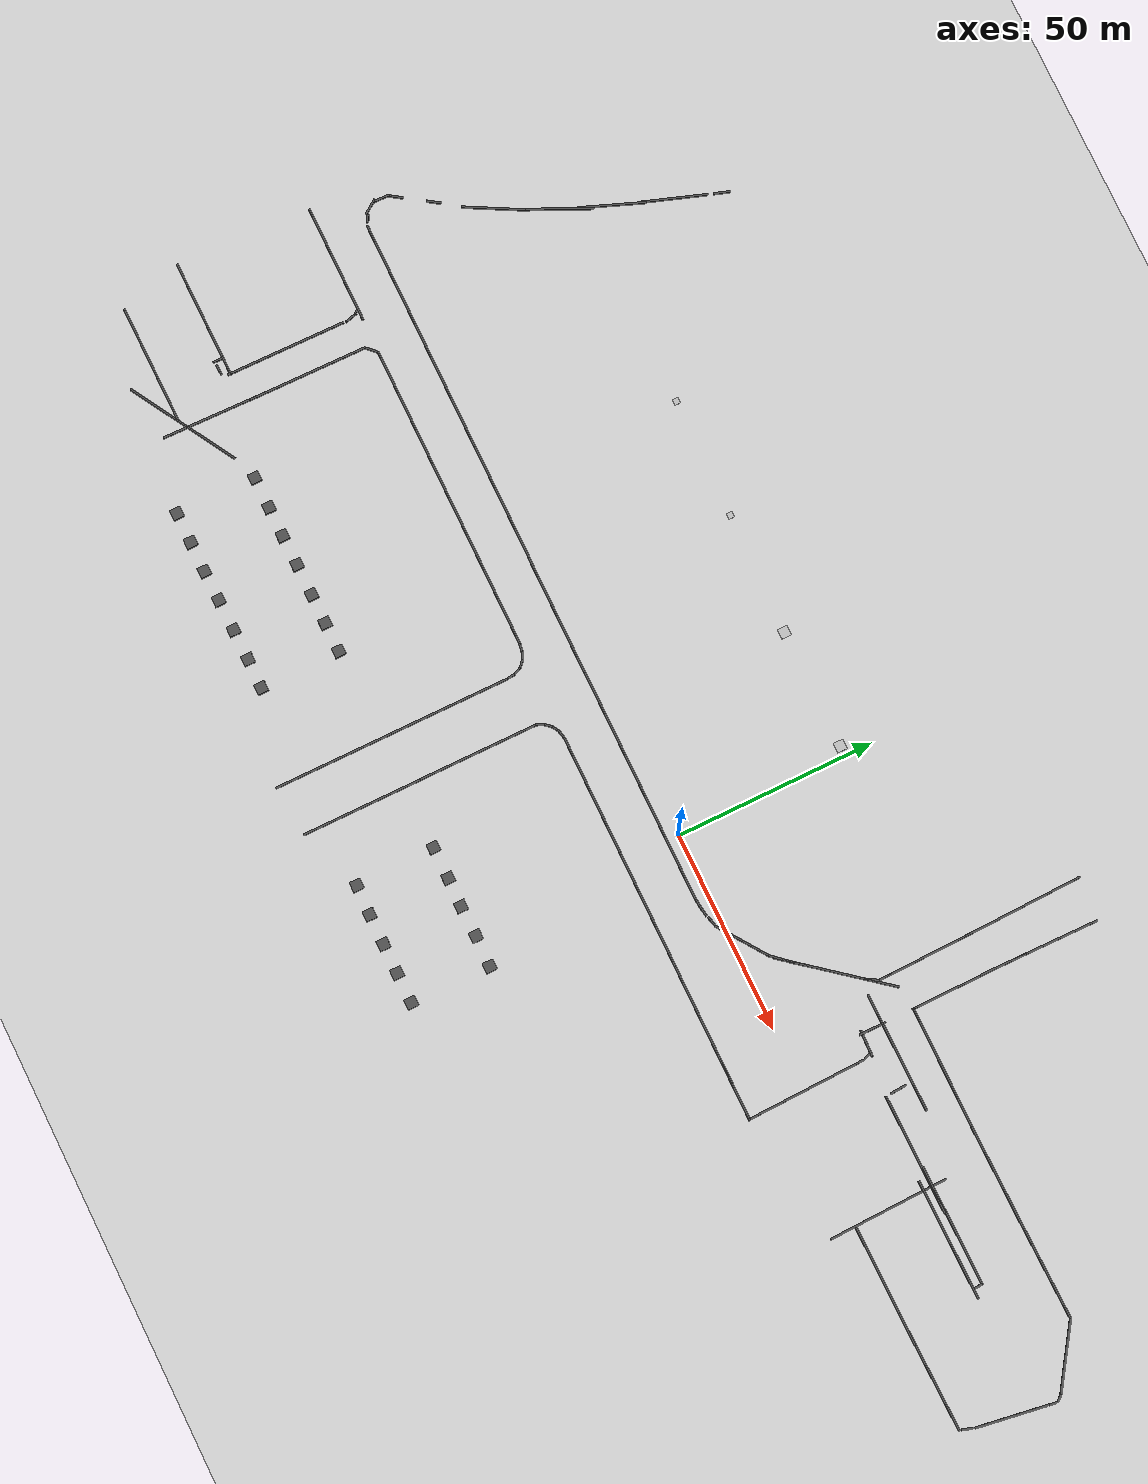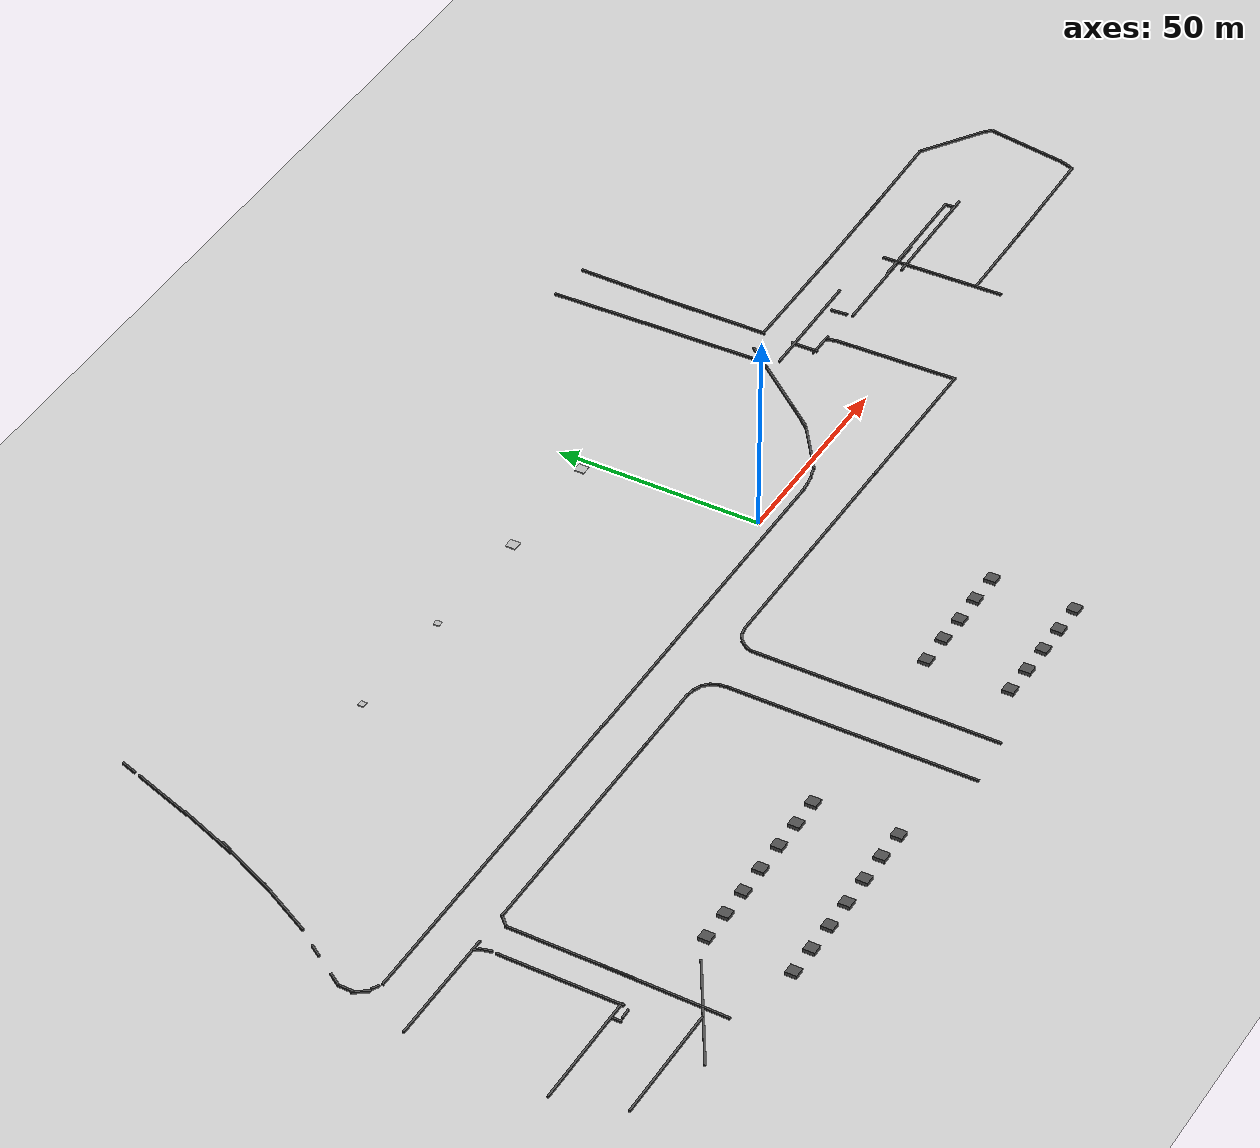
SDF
<sdf version="1.6">
 <world name="default">
  <light name="sun" type="directional">
   <pose>0 0 10 0 -0 0</pose>
   <diffuse>0.8 0.8 0.8 1</diffuse>
   <specular>0.2 0.2 0.2 1</specular>
   <attenuation>
    <range>1000</range>
    <constant>0.9</constant>
    <linear>0.01</linear>
    <quadratic>0.001</quadratic>
   </attenuation>
   <direction>-0.5 0.1 -0.9</direction>
  </light>
  <plugin name="ros_interface_plugin" filename="librotors_gazebo_ros_interface_plugin.so"/>
  <spherical_coordinates>
   <surface_model>EARTH_WGS84</surface_model>
   <latitude_deg>47.3667</latitude_deg>
   <longitude_deg>8.55</longitude_deg>
   <elevation>500</elevation>
   <heading_deg>0</heading_deg>
  </spherical_coordinates>
  <physics name="default_physics" default="0" type="ode">
   <ode>
    <solver>
     <type>quick</type>
     <iters>1000</iters>
     <sor>1.3</sor>
     <use_dynamic_moi_rescaling>0</use_dynamic_moi_rescaling>
    </solver>
    <constraints>
     <cfm>0</cfm>
     <erp>0.2</erp>
     <contact_max_correcting_vel>100</contact_max_correcting_vel>
     <contact_surface_layer>0.001</contact_surface_layer>
    </constraints>
   </ode>
   <max_step_size>0.01</max_step_size>
   <real_time_factor>1</real_time_factor>
   <real_time_update_rate>100</real_time_update_rate>
  </physics>
  <gravity>0 0 -9.8</gravity>
  <magnetic_field>6e-06 2.3e-05 -4.2e-05</magnetic_field>
  <atmosphere type="adiabatic"/>
  <scene><ambient>0.4 0.4 0.4 1</ambient><background>0.7 0.7 0.7 1</background><shadows>1</shadows></scene>
  <audio><device>default</device></audio>
  <model name="my_ground_plane">
   <static>1</static>
   <link name="link">
    <collision name="collision">
     <geometry><plane><normal>0 0 1</normal><size>340 160</size></plane></geometry>
     <surface><friction><ode><mu>100</mu><mu2>50</mu2></ode></friction></surface>
    </collision>
    <visual name="visual">
     <cast_shadows>0</cast_shadows>
     <geometry><plane><normal>0 0 1</normal><size>340 160</size></plane></geometry>
     <material>
      <script>
       <uri>model://my_ground_plane/materials/scripts/my_ground_plane.material</uri>
       <uri>model://my_ground_plane/materials/textures/MyImage.png</uri>
       <name>MyGroundPlane/Image</name>
      </script>
     </material>
    </visual>
   </link>
   <pose>-0.030904 0.011593 0 0 -0 0</pose>
  </model>
  <model name="asphalt_plane_clone">
   <static>1</static>
   <link name="link">
    <collision name="collision"><geometry><box><size>2.63534 2.74716 1.11854</size></box></geometry></collision>
    <visual name="visual">
     <cast_shadows>0</cast_shadows>
     <geometry><box><size>2.63534 2.74716 1.11854</size></box></geometry>
     <material>
      <script>
       <uri>model://asphalt_plane/materials/scripts</uri>
       <uri>model://asphalt_plane/materials/textures</uri>
       <name>vrc/asphalt</name>
      </script>
     </material>
    </visual>
   </link>
   <pose>-80.9015 -52.6284 0 0 -0 0</pose>
  </model>
  <model name="asphalt_plane_clone_0">
   <static>1</static>
   <link name="link">
    <collision name="collision"><geometry><box><size>2.63534 2.74716 1.11854</size></box></geometry></collision>
    <visual name="visual">
     <cast_shadows>0</cast_shadows>
     <geometry><box><size>2.63534 2.74716 1.11854</size></box></geometry>
     <material>
      <script>
       <uri>model://asphalt_plane/materials/scripts</uri>
       <uri>model://asphalt_plane/materials/textures</uri>
       <name>vrc/asphalt</name>
      </script>
     </material>
    </visual>
   </link>
   <pose>-88.3927 -52.6044 0 0 -0 0</pose>
  </model>
  <model name="asphalt_plane_clone_1">
   <static>1</static>
   <link name="link">
    <collision name="collision"><geometry><box><size>2.63534 2.74716 1.11854</size></box></geometry></collision>
    <visual name="visual">
     <cast_shadows>0</cast_shadows>
     <geometry><box><size>2.63534 2.74716 1.11854</size></box></geometry>
     <material>
      <script>
       <uri>model://asphalt_plane/materials/scripts</uri>
       <uri>model://asphalt_plane/materials/textures</uri>
       <name>vrc/asphalt</name>
      </script>
     </material>
    </visual>
   </link>
   <pose>-96.3531 -52.6584 0 0 -0 0</pose>
  </model>
  <model name="asphalt_plane_clone_2">
   <static>1</static>
   <link name="link">
    <collision name="collision"><geometry><box><size>2.63534 2.74716 1.11854</size></box></geometry></collision>
    <visual name="visual">
     <cast_shadows>0</cast_shadows>
     <geometry><box><size>2.63534 2.74716 1.11854</size></box></geometry>
     <material>
      <script>
       <uri>model://asphalt_plane/materials/scripts</uri>
       <uri>model://asphalt_plane/materials/textures</uri>
       <name>vrc/asphalt</name>
      </script>
     </material>
    </visual>
   </link>
   <pose>-104.057 -52.7917 0 0 -0 0</pose>
  </model>
  <model name="asphalt_plane_clone_3">
   <static>1</static>
   <link name="link">
    <collision name="collision"><geometry><box><size>2.63534 2.74716 1.11854</size></box></geometry></collision>
    <visual name="visual">
     <cast_shadows>0</cast_shadows>
     <geometry><box><size>2.63534 2.74716 1.11854</size></box></geometry>
     <material>
      <script>
       <uri>model://asphalt_plane/materials/scripts</uri>
       <uri>model://asphalt_plane/materials/textures</uri>
       <name>vrc/asphalt</name>
      </script>
     </material>
    </visual>
   </link>
   <pose>-111.594 -52.7906 0 0 -0 0</pose>
  </model>
  <model name="asphalt_plane_clone_4">
   <static>1</static>
   <link name="link">
    <collision name="collision"><geometry><box><size>2.63534 2.74716 1.11854</size></box></geometry></collision>
    <visual name="visual">
     <cast_shadows>0</cast_shadows>
     <geometry><box><size>2.63534 2.74716 1.11854</size></box></geometry>
     <material>
      <script>
       <uri>model://asphalt_plane/materials/scripts</uri>
       <uri>model://asphalt_plane/materials/textures</uri>
       <name>vrc/asphalt</name>
      </script>
     </material>
    </visual>
   </link>
   <pose>-112.001 -72.8409 0 0 -0 0</pose>
  </model>
  <model name="asphalt_plane_clone_5">
   <static>1</static>
   <link name="link">
    <collision name="collision"><geometry><box><size>2.63534 2.74716 1.11854</size></box></geometry></collision>
    <visual name="visual">
     <cast_shadows>0</cast_shadows>
     <geometry><box><size>2.63534 2.74716 1.11854</size></box></geometry>
     <material>
      <script>
       <uri>model://asphalt_plane/materials/scripts</uri>
       <uri>model://asphalt_plane/materials/textures</uri>
       <name>vrc/asphalt</name>
      </script>
     </material>
    </visual>
   </link>
   <pose>-119.635 -72.8269 0 0 -0 0</pose>
  </model>
  <model name="asphalt_plane_clone_6">
   <static>1</static>
   <link name="link">
    <collision name="collision"><geometry><box><size>2.63534 2.74716 1.11854</size></box></geometry></collision>
    <visual name="visual">
     <cast_shadows>0</cast_shadows>
     <geometry><box><size>2.63534 2.74716 1.11854</size></box></geometry>
     <material>
      <script>
       <uri>model://asphalt_plane/materials/scripts</uri>
       <uri>model://asphalt_plane/materials/textures</uri>
       <name>vrc/asphalt</name>
      </script>
     </material>
    </visual>
   </link>
   <pose>-119.446 -52.7981 0 0 -0 0</pose>
  </model>
  <model name="asphalt_plane_clone_7">
   <static>1</static>
   <link name="link">
    <collision name="collision"><geometry><box><size>2.63534 2.74716 1.11854</size></box></geometry></collision>
    <visual name="visual">
     <cast_shadows>0</cast_shadows>
     <geometry><box><size>2.63534 2.74716 1.11854</size></box></geometry>
     <material>
      <script>
       <uri>model://asphalt_plane/materials/scripts</uri>
       <uri>model://asphalt_plane/materials/textures</uri>
       <name>vrc/asphalt</name>
      </script>
     </material>
    </visual>
   </link>
   <pose>-104.317 -72.8508 0 0 -0 0</pose>
  </model>
  <model name="asphalt_plane_clone_8">
   <static>1</static>
   <link name="link">
    <collision name="collision"><geometry><box><size>2.63534 2.74716 1.11854</size></box></geometry></collision>
    <visual name="visual">
     <cast_shadows>0</cast_shadows>
     <geometry><box><size>2.63534 2.74716 1.11854</size></box></geometry>
     <material>
      <script>
       <uri>model://asphalt_plane/materials/scripts</uri>
       <uri>model://asphalt_plane/materials/textures</uri>
       <name>vrc/asphalt</name>
      </script>
     </material>
    </visual>
   </link>
   <pose>-96.6624 -72.7284 0 0 -0 0</pose>
  </model>
  <model name="asphalt_plane_clone_9">
   <static>1</static>
   <link name="link">
    <collision name="collision"><geometry><box><size>2.63534 2.74716 1.11854</size></box></geometry></collision>
    <visual name="visual">
     <cast_shadows>0</cast_shadows>
     <geometry><box><size>2.63534 2.74716 1.11854</size></box></geometry>
     <material>
      <script>
       <uri>model://asphalt_plane/materials/scripts</uri>
       <uri>model://asphalt_plane/materials/textures</uri>
       <name>vrc/asphalt</name>
      </script>
     </material>
    </visual>
   </link>
   <pose>-88.723 -72.5998 0 0 -0 0</pose>
  </model>
  <model name="asphalt_plane_clone_10">
   <static>1</static>
   <link name="link">
    <collision name="collision"><geometry><box><size>2.63534 2.74716 1.11854</size></box></geometry></collision>
    <visual name="visual">
     <cast_shadows>0</cast_shadows>
     <geometry><box><size>2.63534 2.74716 1.11854</size></box></geometry>
     <material>
      <script>
       <uri>model://asphalt_plane/materials/scripts</uri>
       <uri>model://asphalt_plane/materials/textures</uri>
       <name>vrc/asphalt</name>
      </script>
     </material>
    </visual>
   </link>
   <pose>-80.9684 -72.5062 0 0 -0 0</pose>
  </model>
  <model name="asphalt_plane_clone_11">
   <static>1</static>
   <link name="link">
    <collision name="collision"><geometry><box><size>2.63534 2.74716 1.11854</size></box></geometry></collision>
    <visual name="visual">
     <cast_shadows>0</cast_shadows>
     <geometry><box><size>2.63534 2.74716 1.11854</size></box></geometry>
     <material>
      <script>
       <uri>model://asphalt_plane/materials/scripts</uri>
       <uri>model://asphalt_plane/materials/textures</uri>
       <name>vrc/asphalt</name>
      </script>
     </material>
    </visual>
   </link>
   <pose>-73.4998 -72.5792 0 0 -0 0</pose>
  </model>
  <model name="asphalt_plane_clone_12">
   <static>1</static>
   <link name="link">
    <collision name="collision"><geometry><box><size>2.63534 2.74716 1.11854</size></box></geometry></collision>
    <visual name="visual">
     <cast_shadows>0</cast_shadows>
     <geometry><box><size>2.63534 2.74716 1.11854</size></box></geometry>
     <material>
      <script>
       <uri>model://asphalt_plane/materials/scripts</uri>
       <uri>model://asphalt_plane/materials/textures</uri>
       <name>vrc/asphalt</name>
      </script>
     </material>
    </visual>
   </link>
   <pose>-22.164 -52.4753 0 0 -0 0</pose>
  </model>
  <model name="asphalt_plane_clone_13">
   <static>1</static>
   <link name="link">
    <collision name="collision"><geometry><box><size>2.63534 2.74716 1.11854</size></box></geometry></collision>
    <visual name="visual">
     <cast_shadows>0</cast_shadows>
     <geometry><box><size>2.63534 2.74716 1.11854</size></box></geometry>
     <material>
      <script>
       <uri>model://asphalt_plane/materials/scripts</uri>
       <uri>model://asphalt_plane/materials/textures</uri>
       <name>vrc/asphalt</name>
      </script>
     </material>
    </visual>
   </link>
   <pose>-21.9225 -72.258 0 0 -0 0</pose>
  </model>
  <model name="asphalt_plane_clone_14">
   <static>1</static>
   <link name="link">
    <collision name="collision"><geometry><box><size>2.63534 2.74716 1.11854</size></box></geometry></collision>
    <visual name="visual">
     <cast_shadows>0</cast_shadows>
     <geometry><box><size>2.63534 2.74716 1.11854</size></box></geometry>
     <material>
      <script>
       <uri>model://asphalt_plane/materials/scripts</uri>
       <uri>model://asphalt_plane/materials/textures</uri>
       <name>vrc/asphalt</name>
      </script>
     </material>
    </visual>
   </link>
   <pose>-14.2398 -52.4606 0 0 -0 0</pose>
  </model>
  <model name="asphalt_plane_clone_15">
   <static>1</static>
   <link name="link">
    <collision name="collision"><geometry><box><size>2.63534 2.74716 1.11854</size></box></geometry></collision>
    <visual name="visual">
     <cast_shadows>0</cast_shadows>
     <geometry><box><size>2.63534 2.74716 1.11854</size></box></geometry>
     <material>
      <script>
       <uri>model://asphalt_plane/materials/scripts</uri>
       <uri>model://asphalt_plane/materials/textures</uri>
       <name>vrc/asphalt</name>
      </script>
     </material>
    </visual>
   </link>
   <pose>-14.4471 -72.5069 0 0 -0 0</pose>
  </model>
  <model name="asphalt_plane_clone_16">
   <static>1</static>
   <link name="link">
    <collision name="collision"><geometry><box><size>2.63534 2.74716 1.11854</size></box></geometry></collision>
    <visual name="visual">
     <cast_shadows>0</cast_shadows>
     <geometry><box><size>2.63534 2.74716 1.11854</size></box></geometry>
     <material>
      <script>
       <uri>model://asphalt_plane/materials/scripts</uri>
       <uri>model://asphalt_plane/materials/textures</uri>
       <name>vrc/asphalt</name>
      </script>
     </material>
    </visual>
   </link>
   <pose>-6.83663 -72.5535 0 0 -0 0</pose>
  </model>
  <model name="asphalt_plane_clone_17">
   <static>1</static>
   <link name="link">
    <collision name="collision"><geometry><box><size>2.63534 2.74716 1.11854</size></box></geometry></collision>
    <visual name="visual">
     <cast_shadows>0</cast_shadows>
     <geometry><box><size>2.63534 2.74716 1.11854</size></box></geometry>
     <material>
      <script>
       <uri>model://asphalt_plane/materials/scripts</uri>
       <uri>model://asphalt_plane/materials/textures</uri>
       <name>vrc/asphalt</name>
      </script>
     </material>
    </visual>
   </link>
   <pose>-6.99306 -52.6304 0 0 -0 0</pose>
  </model>
  <model name="asphalt_plane_clone_18">
   <static>1</static>
   <link name="link">
    <collision name="collision"><geometry><box><size>2.63534 2.74716 1.11854</size></box></geometry></collision>
    <visual name="visual">
     <cast_shadows>0</cast_shadows>
     <geometry><box><size>2.63534 2.74716 1.11854</size></box></geometry>
     <material>
      <script>
       <uri>model://asphalt_plane/materials/scripts</uri>
       <uri>model://asphalt_plane/materials/textures</uri>
       <name>vrc/asphalt</name>
      </script>
     </material>
    </visual>
   </link>
   <pose>0.728778 -52.4849 0 0 -0 0</pose>
  </model>
  <model name="asphalt_plane_clone_19">
   <static>1</static>
   <link name="link">
    <collision name="collision"><geometry><box><size>2.63534 2.74716 1.11854</size></box></geometry></collision>
    <visual name="visual">
     <cast_shadows>0</cast_shadows>
     <geometry><box><size>2.63534 2.74716 1.11854</size></box></geometry>
     <material>
      <script>
       <uri>model://asphalt_plane/materials/scripts</uri>
       <uri>model://asphalt_plane/materials/textures</uri>
       <name>vrc/asphalt</name>
      </script>
     </material>
    </visual>
   </link>
   <pose>0.573218 -72.5643 0 0 -0 0</pose>
  </model>
  <model name="asphalt_plane_clone_20">
   <static>1</static>
   <link name="link">
    <collision name="collision"><geometry><box><size>2.63534 2.74716 1.11854</size></box></geometry></collision>
    <visual name="visual">
     <cast_shadows>0</cast_shadows>
     <geometry><box><size>2.63534 2.74716 1.11854</size></box></geometry>
     <material>
      <script>
       <uri>model://asphalt_plane/materials/scripts</uri>
       <uri>model://asphalt_plane/materials/textures</uri>
       <name>vrc/asphalt</name>
      </script>
     </material>
    </visual>
   </link>
   <pose>8.19452 -72.5444 0 0 -0 0</pose>
  </model>
  <model name="asphalt_plane_clone_21">
   <static>1</static>
   <link name="link">
    <collision name="collision"><geometry><box><size>2.63534 2.74716 1.11854</size></box></geometry></collision>
    <visual name="visual">
     <cast_shadows>0</cast_shadows>
     <geometry><box><size>2.63534 2.74716 1.11854</size></box></geometry>
     <material>
      <script>
       <uri>model://asphalt_plane/materials/scripts</uri>
       <uri>model://asphalt_plane/materials/textures</uri>
       <name>vrc/asphalt</name>
      </script>
     </material>
    </visual>
   </link>
   <pose>8.44148 -52.6245 0 0 -0 0</pose>
  </model>
  <model name="asphalt_box">
   <static>1</static>
   <link name="link">
    <collision name="collision"><geometry><box><size>30 0.5 0.5</size></box></geometry></collision>
    <visual name="visual">
     <cast_shadows>0</cast_shadows>
     <geometry><box><size>30 0.5 0.5</size></box></geometry>
     <material>
      <script>
       <uri>model://asphalt_box/materials/scripts</uri>
       <uri>model://asphalt_box/materials/textures</uri>
       <name>vrc/asphalt</name>
      </script>
     </material>
    </visual>
   </link>
   <pose>-119.499 -13.6834 0 0 -0 0</pose>
  </model>
  <model name="asphalt_box_clone">
   <static>1</static>
   <link name="link">
    <collision name="collision"><geometry><box><size>30 0.5 0.5</size></box></geometry></collision>
    <visual name="visual">
     <cast_shadows>0</cast_shadows>
     <geometry><box><size>30 0.5 0.5</size></box></geometry>
     <material>
      <script>
       <uri>model://asphalt_box/materials/scripts</uri>
       <uri>model://asphalt_box/materials/textures</uri>
       <name>vrc/asphalt</name>
      </script>
     </material>
    </visual>
   </link>
   <pose>-89.583 -13.6887 0 0 -0 0</pose>
  </model>
  <model name="asphalt_box_clone_0">
   <static>1</static>
   <link name="link">
    <collision name="collision"><geometry><box><size>30 0.5 0.5</size></box></geometry></collision>
    <visual name="visual">
     <cast_shadows>0</cast_shadows>
     <geometry><box><size>30 0.5 0.5</size></box></geometry>
     <material>
      <script>
       <uri>model://asphalt_box/materials/scripts</uri>
       <uri>model://asphalt_box/materials/textures</uri>
       <name>vrc/asphalt</name>
      </script>
     </material>
    </visual>
   </link>
   <pose>-71.686 -13.7066 0 0 -0 0</pose>
  </model>
  <model name="asphalt_box_clone_1">
   <static>1</static>
   <link name="link">
    <collision name="collision"><geometry><box><size>30 0.5 0.5</size></box></geometry></collision>
    <visual name="visual">
     <cast_shadows>0</cast_shadows>
     <geometry><box><size>30 0.5 0.5</size></box></geometry>
     <material>
      <script>
       <uri>model://asphalt_box/materials/scripts</uri>
       <uri>model://asphalt_box/materials/textures</uri>
       <name>vrc/asphalt</name>
      </script>
     </material>
    </visual>
   </link>
   <pose>-148.205 -2.93016 0 0 -0 0</pose>
  </model>
  <model name="asphalt_box_clone_2">
   <static>1</static>
   <link name="link">
    <collision name="collision"><geometry><box><size>30 0.5 0.5</size></box></geometry></collision>
    <visual name="visual">
     <cast_shadows>0</cast_shadows>
     <geometry><box><size>30 0.5 0.5</size></box></geometry>
     <material>
      <script>
       <uri>model://asphalt_box/materials/scripts</uri>
       <uri>model://asphalt_box/materials/textures</uri>
       <name>vrc/asphalt</name>
      </script>
     </material>
    </visual>
   </link>
   <pose>-118.911 -2.94896 0 0 -0 0</pose>
  </model>
  <model name="asphalt_box_clone_3">
   <static>1</static>
   <link name="link">
    <collision name="collision"><geometry><box><size>30 0.5 0.5</size></box></geometry></collision>
    <visual name="visual">
     <cast_shadows>0</cast_shadows>
     <geometry><box><size>30 0.5 0.5</size></box></geometry>
     <material>
      <script>
       <uri>model://asphalt_box/materials/scripts</uri>
       <uri>model://asphalt_box/materials/textures</uri>
       <name>vrc/asphalt</name>
      </script>
     </material>
    </visual>
   </link>
   <pose>-89.4003 -2.92809 0 0 -0 0</pose>
  </model>
  <model name="asphalt_box_clone_4">
   <static>1</static>
   <link name="link">
    <collision name="collision"><geometry><box><size>30 0.5 0.5</size></box></geometry></collision>
    <visual name="visual">
     <cast_shadows>0</cast_shadows>
     <geometry><box><size>30 0.5 0.5</size></box></geometry>
     <material>
      <script>
       <uri>model://asphalt_box/materials/scripts</uri>
       <uri>model://asphalt_box/materials/textures</uri>
       <name>vrc/asphalt</name>
      </script>
     </material>
    </visual>
   </link>
   <pose>-59.3918 -3.01745 0 0 -0 0</pose>
  </model>
  <model name="asphalt_box_clone_5">
   <static>1</static>
   <link name="link">
    <collision name="collision"><geometry><box><size>30 0.5 0.5</size></box></geometry></collision>
    <visual name="visual">
     <cast_shadows>0</cast_shadows>
     <geometry><box><size>30 0.5 0.5</size></box></geometry>
     <material>
      <script>
       <uri>model://asphalt_box/materials/scripts</uri>
       <uri>model://asphalt_box/materials/textures</uri>
       <name>vrc/asphalt</name>
      </script>
     </material>
    </visual>
   </link>
   <pose>-29.4262 -2.97591 0 0 -0 0</pose>
  </model>
  <model name="asphalt_box_clone_6">
   <static>1</static>
   <link name="link">
    <collision name="collision"><geometry><box><size>30 0.5 0.5</size></box></geometry></collision>
    <visual name="visual">
     <cast_shadows>0</cast_shadows>
     <geometry><box><size>30 0.5 0.5</size></box></geometry>
     <material>
      <script>
       <uri>model://asphalt_box/materials/scripts</uri>
       <uri>model://asphalt_box/materials/textures</uri>
       <name>vrc/asphalt</name>
      </script>
     </material>
    </visual>
   </link>
   <pose>-17.2656 -13.9828 0 0 -0 0</pose>
  </model>
  <model name="asphalt_box_clone_7">
   <static>1</static>
   <link name="link">
    <collision name="collision"><geometry><box><size>30 0.5 0.5</size></box></geometry></collision>
    <visual name="visual">
     <cast_shadows>0</cast_shadows>
     <geometry><box><size>30 0.5 0.5</size></box></geometry>
     <material>
      <script>
       <uri>model://asphalt_box/materials/scripts</uri>
       <uri>model://asphalt_box/materials/textures</uri>
       <name>vrc/asphalt</name>
      </script>
     </material>
    </visual>
   </link>
   <pose>12.4994 -14.0005 0 0 -0 0</pose>
  </model>
  <model name="asphalt_box_clone_8">
   <static>1</static>
   <link name="link">
    <collision name="collision"><geometry><box><size>30 0.5 0.5</size></box></geometry></collision>
    <visual name="visual">
     <cast_shadows>0</cast_shadows>
     <geometry><box><size>30 0.5 0.5</size></box></geometry>
     <material>
      <script>
       <uri>model://asphalt_box/materials/scripts</uri>
       <uri>model://asphalt_box/materials/textures</uri>
       <name>vrc/asphalt</name>
      </script>
     </material>
    </visual>
   </link>
   <pose>0.187846 -2.97514 0 0 -0 0</pose>
  </model>
  <model name="asphalt_box_clone_9">
   <static>1</static>
   <link name="link">
    <collision name="collision"><geometry><box><size>30 0.5 0.5</size></box></geometry></collision>
    <visual name="visual">
     <cast_shadows>0</cast_shadows>
     <geometry><box><size>30 0.5 0.5</size></box></geometry>
     <material>
      <script>
       <uri>model://asphalt_box/materials/scripts</uri>
       <uri>model://asphalt_box/materials/textures</uri>
       <name>vrc/asphalt</name>
      </script>
     </material>
    </visual>
   </link>
   <pose>42.169 -14.0424 0 0 -0 0</pose>
  </model>
  <model name="asphalt_box_clone_10">
   <static>1</static>
   <link name="link">
    <collision name="collision"><geometry><box><size>30 0.5 0.5</size></box></geometry></collision>
    <visual name="visual">
     <cast_shadows>0</cast_shadows>
     <geometry><box><size>30 0.5 0.5</size></box></geometry>
     <material>
      <script>
       <uri>model://asphalt_box/materials/scripts</uri>
       <uri>model://asphalt_box/materials/textures</uri>
       <name>vrc/asphalt</name>
      </script>
     </material>
    </visual>
   </link>
   <pose>65.7833 0.808671 0 0 0 -1.54232</pose>
  </model>
  <model name="asphalt_box_clone_9_clone">
   <static>1</static>
   <link name="link">
    <collision name="collision"><geometry><box><size>30 0.5 0.5</size></box></geometry></collision>
    <visual name="visual">
     <cast_shadows>0</cast_shadows>
     <geometry><box><size>30 0.5 0.5</size></box></geometry>
     <material>
      <script>
       <uri>model://asphalt_box/materials/scripts</uri>
       <uri>model://asphalt_box/materials/textures</uri>
       <name>vrc/asphalt</name>
      </script>
     </material>
    </visual>
   </link>
   <pose>51.5621 -14.0485 0 0 -0 0</pose>
  </model>
  <model name="asphalt_box_clone_10_clone">
   <static>1</static>
   <link name="link">
    <collision name="collision"><geometry><box><size>30 0.5 0.5</size></box></geometry></collision>
    <visual name="visual">
     <cast_shadows>0</cast_shadows>
     <geometry><box><size>30 0.5 0.5</size></box></geometry>
     <material>
      <script>
       <uri>model://asphalt_box/materials/scripts</uri>
       <uri>model://asphalt_box/materials/textures</uri>
       <name>vrc/asphalt</name>
      </script>
     </material>
    </visual>
   </link>
   <pose>49.501 64.5959 0 0 0 -1.54232</pose>
  </model>
  <model name="asphalt_box_clone_10_clone_0">
   <static>1</static>
   <link name="link">
    <collision name="collision"><geometry><box><size>30 0.5 0.5</size></box></geometry></collision>
    <visual name="visual">
     <cast_shadows>0</cast_shadows>
     <geometry><box><size>30 0.5 0.5</size></box></geometry>
     <material>
      <script>
       <uri>model://asphalt_box/materials/scripts</uri>
       <uri>model://asphalt_box/materials/textures</uri>
       <name>vrc/asphalt</name>
      </script>
     </material>
    </visual>
   </link>
   <pose>50.0394 43.5183 0 0 0 -1.54821</pose>
  </model>
  <model name="asphalt_box_clone_10_clone_clone">
   <static>1</static>
   <link name="link">
    <collision name="collision"><geometry><box><size>30 0.5 0.5</size></box></geometry></collision>
    <visual name="visual">
     <cast_shadows>0</cast_shadows>
     <geometry><box><size>30 0.5 0.5</size></box></geometry>
     <material>
      <script>
       <uri>model://asphalt_box/materials/scripts</uri>
       <uri>model://asphalt_box/materials/textures</uri>
       <name>vrc/asphalt</name>
      </script>
     </material>
    </visual>
   </link>
   <pose>59.7039 63.6002 0 0 0 -1.58298</pose>
  </model>
  <model name="asphalt_box_clone_10_clone_clone_clone">
   <static>1</static>
   <link name="link">
    <collision name="collision"><geometry><box><size>30 0.5 0.5</size></box></geometry></collision>
    <visual name="visual">
     <cast_shadows>0</cast_shadows>
     <geometry><box><size>30 0.5 0.5</size></box></geometry>
     <material>
      <script>
       <uri>model://asphalt_box/materials/scripts</uri>
       <uri>model://asphalt_box/materials/textures</uri>
       <name>vrc/asphalt</name>
      </script>
     </material>
    </visual>
   </link>
   <pose>59.673 45.8294 0 0 0 -1.56625</pose>
  </model>
  <model name="asphalt_box_clone_10_clone_1">
   <static>1</static>
   <link name="link">
    <collision name="collision"><geometry><box><size>30 0.5 0.5</size></box></geometry></collision>
    <visual name="visual">
     <cast_shadows>0</cast_shadows>
     <geometry><box><size>30 0.5 0.5</size></box></geometry>
     <material>
      <script>
       <uri>model://asphalt_box/materials/scripts</uri>
       <uri>model://asphalt_box/materials/textures</uri>
       <name>vrc/asphalt</name>
      </script>
     </material>
    </visual>
   </link>
   <pose>-37.8676 -33.5616 0 0 0 -1.57348</pose>
  </model>
  <model name="asphalt_box_clone_10_clone_1_clone">
   <static>1</static>
   <link name="link">
    <collision name="collision"><geometry><box><size>30 0.5 0.5</size></box></geometry></collision>
    <visual name="visual">
     <cast_shadows>0</cast_shadows>
     <geometry><box><size>30 0.5 0.5</size></box></geometry>
     <material>
      <script>
       <uri>model://asphalt_box/materials/scripts</uri>
       <uri>model://asphalt_box/materials/textures</uri>
       <name>vrc/asphalt</name>
      </script>
     </material>
    </visual>
   </link>
   <pose>-37.9053 -63.3857 0 0 0 -1.57348</pose>
  </model>
  <model name="asphalt_box_clone_10_clone_1_clone_0">
   <static>1</static>
   <link name="link">
    <collision name="collision"><geometry><box><size>30 0.5 0.5</size></box></geometry></collision>
    <visual name="visual">
     <cast_shadows>0</cast_shadows>
     <geometry><box><size>30 0.5 0.5</size></box></geometry>
     <material>
      <script>
       <uri>model://asphalt_box/materials/scripts</uri>
       <uri>model://asphalt_box/materials/textures</uri>
       <name>vrc/asphalt</name>
      </script>
     </material>
    </visual>
   </link>
   <pose>-50.5608 -34.8173 0 0 0 -1.57348</pose>
  </model>
  <model name="asphalt_box_clone_10_clone_1_clone_1">
   <static>1</static>
   <link name="link">
    <collision name="collision"><geometry><box><size>30 0.5 0.5</size></box></geometry></collision>
    <visual name="visual">
     <cast_shadows>0</cast_shadows>
     <geometry><box><size>30 0.5 0.5</size></box></geometry>
     <material>
      <script>
       <uri>model://asphalt_box/materials/scripts</uri>
       <uri>model://asphalt_box/materials/textures</uri>
       <name>vrc/asphalt</name>
      </script>
     </material>
    </visual>
   </link>
   <pose>-50.6193 -64.5106 0 0 0 -1.57348</pose>
  </model>
  <model name="asphalt_box_clone_10_clone_1_clone_1_clone">
   <static>1</static>
   <link name="link">
    <collision name="collision"><geometry><box><size>30 0.5 0.5</size></box></geometry></collision>
    <visual name="visual">
     <cast_shadows>0</cast_shadows>
     <geometry><box><size>30 0.5 0.5</size></box></geometry>
     <material>
      <script>
       <uri>model://asphalt_box/materials/scripts</uri>
       <uri>model://asphalt_box/materials/textures</uri>
       <name>vrc/asphalt</name>
      </script>
     </material>
    </visual>
   </link>
   <pose>-136.791 -30.8262 0 0 0 -1.58301</pose>
  </model>
  <model name="asphalt_box_clone_10_clone_1_clone_1_clone_0">
   <static>1</static>
   <link name="link">
    <collision name="collision"><geometry><box><size>29.9999 0.5 0.5</size></box></geometry></collision>
    <visual name="visual">
     <cast_shadows>0</cast_shadows>
     <geometry><box><size>29.9999 0.5 0.5</size></box></geometry>
     <material>
      <script>
       <uri>model://asphalt_box/materials/scripts</uri>
       <uri>model://asphalt_box/materials/textures</uri>
       <name>vrc/asphalt</name>
      </script>
     </material>
    </visual>
   </link>
   <pose>-137.183 -53.1222 0 0 0 -1.59196</pose>
  </model>
  <model name="asphalt_box_clone_10_clone_1_clone_1_clone_1">
   <static>1</static>
   <link name="link">
    <collision name="collision"><geometry><box><size>30 0.5 0.5</size></box></geometry></collision>
    <visual name="visual">
     <cast_shadows>0</cast_shadows>
     <geometry><box><size>30 0.5 0.5</size></box></geometry>
     <material>
      <script>
       <uri>model://asphalt_box/materials/scripts</uri>
       <uri>model://asphalt_box/materials/textures</uri>
       <name>vrc/asphalt</name>
      </script>
     </material>
    </visual>
   </link>
   <pose>-154.842 -63.247 0 0 0 -3.13563</pose>
  </model>
  <model name="asphalt_box_clone_10_clone_1_clone_1_clone_1_clone">
   <static>1</static>
   <link name="link">
    <collision name="collision"><geometry><box><size>30 0.5 0.5</size></box></geometry></collision>
    <visual name="visual">
     <cast_shadows>0</cast_shadows>
     <geometry><box><size>30 0.5 0.5</size></box></geometry>
     <material>
      <script>
       <uri>model://asphalt_box/materials/scripts</uri>
       <uri>model://asphalt_box/materials/textures</uri>
       <name>vrc/asphalt</name>
      </script>
     </material>
    </visual>
   </link>
   <pose>-138.599 -62.5336 0 0 0 -2.61025</pose>
  </model>
  <model name="asphalt_box_clone_10_clone_1_clone_1_clone_1_clone_0">
   <static>1</static>
   <link name="link">
    <collision name="collision"><geometry><box><size>29.9999 0.5 0.5</size></box></geometry></collision>
    <visual name="visual">
     <cast_shadows>0</cast_shadows>
     <geometry><box><size>29.9999 0.5 0.5</size></box></geometry>
     <material>
      <script>
       <uri>model://asphalt_box/materials/scripts</uri>
       <uri>model://asphalt_box/materials/textures</uri>
       <name>vrc/asphalt</name>
      </script>
     </material>
    </visual>
   </link>
   <pose>-159.297 -47.4047 0 0 0 -3.13563</pose>
  </model>
  <model name="asphalt_box_clone_10_clone_1_clone_1_clone_1_clone_clone">
   <static>1</static>
   <link name="link">
    <collision name="collision"><geometry><box><size>2.80752 0.5 0.5</size></box></geometry></collision>
    <visual name="visual">
     <cast_shadows>0</cast_shadows>
     <geometry><box><size>2.80752 0.5 0.5</size></box></geometry>
     <material>
      <script>
       <uri>model://asphalt_box/materials/scripts</uri>
       <uri>model://asphalt_box/materials/textures</uri>
       <name>vrc/asphalt</name>
      </script>
     </material>
    </visual>
   </link>
   <pose>-148.926 -48.4817 0 0 0 -1.57709</pose>
  </model>
  <model name="asphalt_box_clone_10_clone_1_clone_1_clone_1_clone_clone_0">
   <static>1</static>
   <link name="link">
    <collision name="collision"><geometry><box><size>2.80751 0.5 0.5</size></box></geometry></collision>
    <visual name="visual">
     <cast_shadows>0</cast_shadows>
     <geometry><box><size>2.80751 0.5 0.5</size></box></geometry>
     <material>
      <script>
       <uri>model://asphalt_box/materials/scripts</uri>
       <uri>model://asphalt_box/materials/textures</uri>
       <name>vrc/asphalt</name>
      </script>
     </material>
    </visual>
   </link>
   <pose>-146.686 -49.3456 0 0 0 -3.11123</pose>
  </model>
  <model name="asphalt_box_clone_10_clone_1_clone_1_clone_clone">
   <static>1</static>
   <link name="link">
    <collision name="collision"><geometry><box><size>30.0001 0.5 0.5</size></box></geometry></collision>
    <visual name="visual">
     <cast_shadows>0</cast_shadows>
     <geometry><box><size>30.0001 0.5 0.5</size></box></geometry>
     <material>
      <script>
       <uri>model://asphalt_box/materials/scripts</uri>
       <uri>model://asphalt_box/materials/textures</uri>
       <name>vrc/asphalt</name>
      </script>
     </material>
    </visual>
   </link>
   <pose>-144.527 -33.0445 0 0 0 -1.58301</pose>
  </model>
  <model name="asphalt_box_clone_10_clone_1_clone_1_clone_1_clone_clone_1">
   <static>1</static>
   <link name="link">
    <collision name="collision"><geometry><box><size>2.80752 0.5 0.5</size></box></geometry></collision>
    <visual name="visual">
     <cast_shadows>0</cast_shadows>
     <geometry><box><size>2.80752 0.5 0.5</size></box></geometry>
     <material>
      <script>
       <uri>model://asphalt_box/materials/scripts</uri>
       <uri>model://asphalt_box/materials/textures</uri>
       <name>vrc/asphalt</name>
      </script>
     </material>
    </visual>
   </link>
   <pose>-135.43 -14.8484 0 0 0 -2.35698</pose>
  </model>
  <model name="asphalt_box_clone_10_clone_1_clone_1_clone_1_clone_clone_1_clone">
   <static>1</static>
   <link name="link">
    <collision name="collision"><geometry><box><size>3.16201 0.5 0.5</size></box></geometry></collision>
    <visual name="visual">
     <cast_shadows>0</cast_shadows>
     <geometry><box><size>3.16201 0.5 0.5</size></box></geometry>
     <material>
      <script>
       <uri>model://asphalt_box/materials/scripts</uri>
       <uri>model://asphalt_box/materials/textures</uri>
       <name>vrc/asphalt</name>
      </script>
     </material>
    </visual>
   </link>
   <pose>-144.559 -15.893 0 0 -0 1.83153</pose>
  </model>
  <model name="asphalt_box_clone_11">
   <static>1</static>
   <link name="link">
    <collision name="collision"><geometry><box><size>30 0.5 0.5</size></box></geometry></collision>
    <visual name="visual">
     <cast_shadows>0</cast_shadows>
     <geometry><box><size>30 0.5 0.5</size></box></geometry>
     <material>
      <script>
       <uri>model://asphalt_box/materials/scripts</uri>
       <uri>model://asphalt_box/materials/textures</uri>
       <name>vrc/asphalt</name>
      </script>
     </material>
    </visual>
   </link>
   <pose>-157.845 -13.568 0 0 -0 0</pose>
  </model>
  <model name="asphalt_box_clone_10_clone_1_clone_1_clone_1_clone_clone_1_clone_clone">
   <static>1</static>
   <link name="link">
    <collision name="collision"><geometry><box><size>1.74763 0.5 0.5</size></box></geometry></collision>
    <visual name="visual">
     <cast_shadows>0</cast_shadows>
     <geometry><box><size>1.74763 0.5 0.5</size></box></geometry>
     <material>
      <script>
       <uri>model://asphalt_box/materials/scripts</uri>
       <uri>model://asphalt_box/materials/textures</uri>
       <name>vrc/asphalt</name>
      </script>
     </material>
    </visual>
   </link>
   <pose>-145.29 -14.2704 0 0 -0 2.20599</pose>
  </model>
  <model name="asphalt_box_clone_10_clone_1_clone_1_clone_1_clone_clone_1_clone_clone_clone">
   <static>1</static>
   <link name="link">
    <collision name="collision"><geometry><box><size>1.96342 0.5 0.5</size></box></geometry></collision>
    <visual name="visual">
     <cast_shadows>0</cast_shadows>
     <geometry><box><size>1.96342 0.5 0.5</size></box></geometry>
     <material>
      <script>
       <uri>model://asphalt_box/materials/scripts</uri>
       <uri>model://asphalt_box/materials/textures</uri>
       <name>vrc/asphalt</name>
      </script>
     </material>
    </visual>
   </link>
   <pose>-55.9791 -13.8806 0 0 -0 3.00079</pose>
  </model>
  <model name="asphalt_box_clone_10_clone_1_clone_1_clone_1_clone_clone_1_clone_clone_clone_clone">
   <static>1</static>
   <link name="link">
    <collision name="collision"><geometry><box><size>1.96342 0.5 0.5</size></box></geometry></collision>
    <visual name="visual">
     <cast_shadows>0</cast_shadows>
     <geometry><box><size>1.96342 0.5 0.5</size></box></geometry>
     <material>
      <script>
       <uri>model://asphalt_box/materials/scripts</uri>
       <uri>model://asphalt_box/materials/textures</uri>
       <name>vrc/asphalt</name>
      </script>
     </material>
    </visual>
   </link>
   <pose>-54.0526 -14.4119 0 0 -0 2.76268</pose>
  </model>
  <model name="asphalt_box_clone_10_clone_1_clone_1_clone_1_clone_clone_1_clone_clone_clone_clone_clone">
   <static>1</static>
   <link name="link">
    <collision name="collision"><geometry><box><size>1.96342 0.5 0.5</size></box></geometry></collision>
    <visual name="visual">
     <cast_shadows>0</cast_shadows>
     <geometry><box><size>1.96342 0.5 0.5</size></box></geometry>
     <material>
      <script>
       <uri>model://asphalt_box/materials/scripts</uri>
       <uri>model://asphalt_box/materials/textures</uri>
       <name>vrc/asphalt</name>
      </script>
     </material>
    </visual>
   </link>
   <pose>-52.3284 -15.4324 0 0 -0 2.39482</pose>
  </model>
  <model name="asphalt_box_clone_10_clone_1_clone_1_clone_1_clone_clone_1_clone_clone_clone_clone_clone_clone">
   <static>1</static>
   <link name="link">
    <collision name="collision"><geometry><box><size>1.96342 0.5 0.5</size></box></geometry></collision>
    <visual name="visual">
     <cast_shadows>0</cast_shadows>
     <geometry><box><size>1.96342 0.5 0.5</size></box></geometry>
     <material>
      <script>
       <uri>model://asphalt_box/materials/scripts</uri>
       <uri>model://asphalt_box/materials/textures</uri>
       <name>vrc/asphalt</name>
      </script>
     </material>
    </visual>
   </link>
   <pose>-51.19 -16.9804 0 0 -0 1.98058</pose>
  </model>
  <model name="asphalt_box_clone_10_clone_1_clone_1_clone_1_clone_clone_1_clone_clone_clone_clone_clone_clone_clone">
   <static>1</static>
   <link name="link">
    <collision name="collision"><geometry><box><size>1.96342 0.5 0.5</size></box></geometry></collision>
    <visual name="visual">
     <cast_shadows>0</cast_shadows>
     <geometry><box><size>1.96342 0.5 0.5</size></box></geometry>
     <material>
      <script>
       <uri>model://asphalt_box/materials/scripts</uri>
       <uri>model://asphalt_box/materials/textures</uri>
       <name>vrc/asphalt</name>
      </script>
     </material>
    </visual>
   </link>
   <pose>-50.6506 -18.781 0 0 -0 1.66057</pose>
  </model>
  <model name="asphalt_box_clone_10_clone_1_clone_1_clone_1_clone_clone_1_clone_clone_clone_clone_clone_clone_clone_0">
   <static>1</static>
   <link name="link">
    <collision name="collision"><geometry><box><size>1.96342 0.5 0.5</size></box></geometry></collision>
    <visual name="visual">
     <cast_shadows>0</cast_shadows>
     <geometry><box><size>1.96342 0.5 0.5</size></box></geometry>
     <material>
      <script>
       <uri>model://asphalt_box/materials/scripts</uri>
       <uri>model://asphalt_box/materials/textures</uri>
       <name>vrc/asphalt</name>
      </script>
     </material>
    </visual>
   </link>
   <pose>-33.2112 -14.2012 0 0 -0 0.198974</pose>
  </model>
  <model name="asphalt_box_clone_10_clone_1_clone_1_clone_1_clone_clone_1_clone_clone_clone_clone_clone_clone_clone_0_clone">
   <static>1</static>
   <link name="link">
    <collision name="collision"><geometry><box><size>1.96342 0.5 0.5</size></box></geometry></collision>
    <visual name="visual">
     <cast_shadows>0</cast_shadows>
     <geometry><box><size>1.96342 0.5 0.5</size></box></geometry>
     <material>
      <script>
       <uri>model://asphalt_box/materials/scripts</uri>
       <uri>model://asphalt_box/materials/textures</uri>
       <name>vrc/asphalt</name>
      </script>
     </material>
    </visual>
   </link>
   <pose>-34.9829 -14.8506 0 0 -0 0.549721</pose>
  </model>
  <model name="asphalt_box_clone_10_clone_1_clone_1_clone_1_clone_clone_1_clone_clone_clone_clone_clone_clone_clone_0_clone_clone">
   <static>1</static>
   <link name="link">
    <collision name="collision"><geometry><box><size>1.96342 0.5 0.5</size></box></geometry></collision>
    <visual name="visual">
     <cast_shadows>0</cast_shadows>
     <geometry><box><size>1.96342 0.5 0.5</size></box></geometry>
     <material>
      <script>
       <uri>model://asphalt_box/materials/scripts</uri>
       <uri>model://asphalt_box/materials/textures</uri>
       <name>vrc/asphalt</name>
      </script>
     </material>
    </visual>
   </link>
   <pose>-36.4688 -16.0891 0 0 -0 0.896639</pose>
  </model>
  <model name="asphalt_box_clone_10_clone_1_clone_1_clone_1_clone_clone_1_clone_clone_clone_clone_clone_clone_clone_0_clone_clone_clone">
   <static>1</static>
   <link name="link">
    <collision name="collision"><geometry><box><size>1.96342 0.5 0.5</size></box></geometry></collision>
    <visual name="visual">
     <cast_shadows>0</cast_shadows>
     <geometry><box><size>1.96342 0.5 0.5</size></box></geometry>
     <material>
      <script>
       <uri>model://asphalt_box/materials/scripts</uri>
       <uri>model://asphalt_box/materials/textures</uri>
       <name>vrc/asphalt</name>
      </script>
     </material>
    </visual>
   </link>
   <pose>-37.5423 -17.7303 0 0 -0 1.19727</pose>
  </model>
  <model name="asphalt_box_clone_9_clone_clone">
   <static>1</static>
   <link name="link">
    <collision name="collision"><geometry><box><size>30 0.5 0.5</size></box></geometry></collision>
    <visual name="visual">
     <cast_shadows>0</cast_shadows>
     <geometry><box><size>30 0.5 0.5</size></box></geometry>
     <material>
      <script>
       <uri>model://asphalt_box/materials/scripts</uri>
       <uri>model://asphalt_box/materials/textures</uri>
       <name>vrc/asphalt</name>
      </script>
     </material>
    </visual>
   </link>
   <pose>74.7872 31.2463 0 0 -0 0</pose>
  </model>
  <model name="asphalt_box_clone_9_clone_clone_0">
   <static>1</static>
   <link name="link">
    <collision name="collision"><geometry><box><size>30 0.5 0.5</size></box></geometry></collision>
    <visual name="visual">
     <cast_shadows>0</cast_shadows>
     <geometry><box><size>30 0.5 0.5</size></box></geometry>
     <material>
      <script>
       <uri>model://asphalt_box/materials/scripts</uri>
       <uri>model://asphalt_box/materials/textures</uri>
       <name>vrc/asphalt</name>
      </script>
     </material>
    </visual>
   </link>
   <pose>104.684 31.4537 0 0 -0 0.016111</pose>
  </model>
  <model name="asphalt_box_clone_9_clone_clone_1">
   <static>1</static>
   <link name="link">
    <collision name="collision"><geometry><box><size>30 0.5 0.5</size></box></geometry></collision>
    <visual name="visual">
     <cast_shadows>0</cast_shadows>
     <geometry><box><size>30 0.5 0.5</size></box></geometry>
     <material>
      <script>
       <uri>model://asphalt_box/materials/scripts</uri>
       <uri>model://asphalt_box/materials/textures</uri>
       <name>vrc/asphalt</name>
      </script>
     </material>
    </visual>
   </link>
   <pose>123.741 31.7823 0 0 -0 0.022248</pose>
  </model>
  <model name="asphalt_box_clone_9_clone_clone_1_clone">
   <static>1</static>
   <link name="link">
    <collision name="collision"><geometry><box><size>30 0.5 0.5</size></box></geometry></collision>
    <visual name="visual">
     <cast_shadows>0</cast_shadows>
     <geometry><box><size>30 0.5 0.5</size></box></geometry>
     <material>
      <script>
       <uri>model://asphalt_box/materials/scripts</uri>
       <uri>model://asphalt_box/materials/textures</uri>
       <name>vrc/asphalt</name>
      </script>
     </material>
    </visual>
   </link>
   <pose>113.953 -2.71493 0 0 -0 0.012015</pose>
  </model>
  <model name="asphalt_box_clone_9_clone_clone_1_clone_clone">
   <static>1</static>
   <link name="link">
    <collision name="collision"><geometry><box><size>30 0.5 0.5</size></box></geometry></collision>
    <visual name="visual">
     <cast_shadows>0</cast_shadows>
     <geometry><box><size>30 0.5 0.5</size></box></geometry>
     <material>
      <script>
       <uri>model://asphalt_box/materials/scripts</uri>
       <uri>model://asphalt_box/materials/textures</uri>
       <name>vrc/asphalt</name>
      </script>
     </material>
    </visual>
   </link>
   <pose>135.515 -2.33478 0 0 -0 0.020249</pose>
  </model>
  <model name="asphalt_box_clone_10_clone_2">
   <static>1</static>
   <link name="link">
    <collision name="collision"><geometry><box><size>29.9999 0.5 0.5</size></box></geometry></collision>
    <visual name="visual">
     <cast_shadows>0</cast_shadows>
     <geometry><box><size>29.9999 0.5 0.5</size></box></geometry>
     <material>
      <script>
       <uri>model://asphalt_box/materials/scripts</uri>
       <uri>model://asphalt_box/materials/textures</uri>
       <name>vrc/asphalt</name>
      </script>
     </material>
    </visual>
   </link>
   <pose>98.4703 5.66937 0 0 0 -1.54232</pose>
  </model>
  <model name="asphalt_box_clone_10_clone_2_clone">
   <static>1</static>
   <link name="link">
    <collision name="collision"><geometry><box><size>17.6232 0.5 0.5</size></box></geometry></collision>
    <visual name="visual">
     <cast_shadows>0</cast_shadows>
     <geometry><box><size>17.6232 0.5 0.5</size></box></geometry>
     <material>
      <script>
       <uri>model://asphalt_box/materials/scripts</uri>
       <uri>model://asphalt_box/materials/textures</uri>
       <name>vrc/asphalt</name>
      </script>
     </material>
    </visual>
   </link>
   <pose>152.733 10.1055 0 0 0 -1.72192</pose>
  </model>
  <model name="asphalt_box_clone_10_clone_2_clone_clone">
   <static>1</static>
   <link name="link">
    <collision name="collision"><geometry><box><size>17.6232 0.5 0.5</size></box></geometry></collision>
    <visual name="visual">
     <cast_shadows>0</cast_shadows>
     <geometry><box><size>17.6232 0.5 0.5</size></box></geometry>
     <material>
      <script>
       <uri>model://asphalt_box/materials/scripts</uri>
       <uri>model://asphalt_box/materials/textures</uri>
       <name>vrc/asphalt</name>
      </script>
     </material>
    </visual>
   </link>
   <pose>145.987 27.2357 0 0 0 -0.593263</pose>
  </model>
  <model name="asphalt_box_clone_10_clone_1_clone_1_clone_1_clone_clone_1_clone_clone_clone_clone_clone_clone_clone_0_clone_clone_0">
   <static>1</static>
   <link name="link">
    <collision name="collision"><geometry><box><size>1.96342 0.5 0.5</size></box></geometry></collision>
    <visual name="visual">
     <cast_shadows>0</cast_shadows>
     <geometry><box><size>1.96342 0.5 0.5</size></box></geometry>
     <material>
      <script>
       <uri>model://asphalt_box/materials/scripts</uri>
       <uri>model://asphalt_box/materials/textures</uri>
       <name>vrc/asphalt</name>
      </script>
     </material>
    </visual>
   </link>
   <pose>153.723 21.7934 0 0 0 -0.81996</pose>
  </model>
  <model name="asphalt_box_clone_10_clone_1_clone_1_clone_1_clone_clone_1_clone_clone_clone_clone_clone_clone_clone_0_clone_clone_0_clone">
   <static>1</static>
   <link name="link">
    <collision name="collision"><geometry><box><size>1.96342 0.5 0.5</size></box></geometry></collision>
    <visual name="visual">
     <cast_shadows>0</cast_shadows>
     <geometry><box><size>1.96342 0.5 0.5</size></box></geometry>
     <material>
      <script>
       <uri>model://asphalt_box/materials/scripts</uri>
       <uri>model://asphalt_box/materials/textures</uri>
       <name>vrc/asphalt</name>
      </script>
     </material>
    </visual>
   </link>
   <pose>154.242 19.9731 0 0 0 -1.72359</pose>
  </model>
  <model name="asphalt_box_clone_9_clone_clone_1_clone_clone_0">
   <static>1</static>
   <link name="link">
    <collision name="collision"><geometry><box><size>30 0.5 0.5</size></box></geometry></collision>
    <visual name="visual">
     <cast_shadows>0</cast_shadows>
     <geometry><box><size>30 0.5 0.5</size></box></geometry>
     <material>
      <script>
       <uri>model://asphalt_box/materials/scripts</uri>
       <uri>model://asphalt_box/materials/textures</uri>
       <name>vrc/asphalt</name>
      </script>
     </material>
    </visual>
   </link>
   <pose>90.0352 16.7233 0 0 -0 0.012015</pose>
  </model>
  <model name="asphalt_box_clone_9_clone_clone_1_clone_clone_1">
   <static>1</static>
   <link name="link">
    <collision name="collision"><geometry><box><size>30 0.5 0.5</size></box></geometry></collision>
    <visual name="visual">
     <cast_shadows>0</cast_shadows>
     <geometry><box><size>30 0.5 0.5</size></box></geometry>
     <material>
      <script>
       <uri>model://asphalt_box/materials/scripts</uri>
       <uri>model://asphalt_box/materials/textures</uri>
       <name>vrc/asphalt</name>
      </script>
     </material>
    </visual>
   </link>
   <pose>108.274 17.2216 0 0 -0 0.012015</pose>
  </model>
  <model name="asphalt_box_clone_10_clone_1_clone_1_clone_1_clone_clone_1_clone_clone_clone_clone_clone_clone_clone_0_clone_clone_0_clone_0">
   <static>1</static>
   <link name="link">
    <collision name="collision"><geometry><box><size>1.96342 0.5 0.5</size></box></geometry></collision>
    <visual name="visual">
     <cast_shadows>0</cast_shadows>
     <geometry><box><size>1.96342 0.5 0.5</size></box></geometry>
     <material>
      <script>
       <uri>model://asphalt_box/materials/scripts</uri>
       <uri>model://asphalt_box/materials/textures</uri>
       <name>vrc/asphalt</name>
      </script>
     </material>
    </visual>
   </link>
   <pose>123.12 16.3757 0 0 0 -1.53712</pose>
  </model>
  <model name="asphalt_box_clone_9_clone_clone_1_clone_clone_1_clone">
   <static>1</static>
   <link name="link">
    <collision name="collision"><geometry><box><size>30 0.5 0.5</size></box></geometry></collision>
    <visual name="visual">
     <cast_shadows>0</cast_shadows>
     <geometry><box><size>30 0.5 0.5</size></box></geometry>
     <material>
      <script>
       <uri>model://asphalt_box/materials/scripts</uri>
       <uri>model://asphalt_box/materials/textures</uri>
       <name>vrc/asphalt</name>
      </script>
     </material>
    </visual>
   </link>
   <pose>110.717 14.94 0 0 -0 0.012015</pose>
  </model>
  <model name="asphalt_box_clone_9_clone_clone_1_clone_clone_0_clone">
   <static>1</static>
   <link name="link">
    <collision name="collision"><geometry><box><size>30.0001 0.5 0.5</size></box></geometry></collision>
    <visual name="visual">
     <cast_shadows>0</cast_shadows>
     <geometry><box><size>30.0001 0.5 0.5</size></box></geometry>
     <material>
      <script>
       <uri>model://asphalt_box/materials/scripts</uri>
       <uri>model://asphalt_box/materials/textures</uri>
       <name>vrc/asphalt</name>
      </script>
     </material>
    </visual>
   </link>
   <pose>67.2328 23.3572 0 0 -0 0.012015</pose>
  </model>
  <model name="asphalt_box_clone_10_clone_1_clone_1_clone_1_clone_clone_1_clone_clone_clone_clone_clone_clone_clone_0_clone_clone_0_clone_clone">
   <static>1</static>
   <link name="link">
    <collision name="collision"><geometry><box><size>2.61111 0.5 0.5</size></box></geometry></collision>
    <visual name="visual">
     <cast_shadows>0</cast_shadows>
     <geometry><box><size>2.61111 0.5 0.5</size></box></geometry>
     <material>
      <script>
       <uri>model://asphalt_box/materials/scripts</uri>
       <uri>model://asphalt_box/materials/textures</uri>
       <name>vrc/asphalt</name>
      </script>
     </material>
    </visual>
   </link>
   <pose>150.846 -0.212844 0 0.062634 0.010235 -1.88536</pose>
  </model>
  <model name="asphalt_box_clone_10_clone_1_clone_1_clone_1_clone_clone_1_clone_clone_clone_clone_clone_clone_clone_0_clone_clone_0_clone_clone_clone">
   <static>1</static>
   <link name="link">
    <collision name="collision"><geometry><box><size>4.13253 0.5 0.5</size></box></geometry></collision>
    <visual name="visual">
     <cast_shadows>0</cast_shadows>
     <geometry><box><size>4.13253 0.5 0.5</size></box></geometry>
     <material>
      <script>
       <uri>model://asphalt_box/materials/scripts</uri>
       <uri>model://asphalt_box/materials/textures</uri>
       <name>vrc/asphalt</name>
      </script>
     </material>
    </visual>
   </link>
   <pose>74.9142 19.8516 0 0.061948 -0.013798 -1.50471</pose>
  </model>
  <model name="asphalt_box_clone_10_clone_1_clone_1_clone_1_clone_clone_1_clone_clone_clone_clone_clone_clone_clone_0_clone_clone_0_clone_clone_clone_clone">
   <static>1</static>
   <link name="link">
    <collision name="collision"><geometry><box><size>6.76726 0.5 0.5</size></box></geometry></collision>
    <visual name="visual">
     <cast_shadows>0</cast_shadows>
     <geometry><box><size>6.76726 0.5 0.5</size></box></geometry>
     <material>
      <script>
       <uri>model://asphalt_box/materials/scripts</uri>
       <uri>model://asphalt_box/materials/textures</uri>
       <name>vrc/asphalt</name>
      </script>
     </material>
    </visual>
   </link>
   <pose>59.7736 20.6735 0 0.06275 -0.009499 -1.57355</pose>
  </model>
  <model name="asphalt_box_clone_10_clone_1_clone_1_clone_1_clone_clone_1_clone_clone_clone_clone_clone_clone_clone_0_clone_clone_0_clone_clone_clone_clone_0">
   <static>1</static>
   <link name="link">
    <collision name="collision"><geometry><box><size>6.76725 0.5 0.5</size></box></geometry></collision>
    <visual name="visual">
     <cast_shadows>0</cast_shadows>
     <geometry><box><size>6.76725 0.5 0.5</size></box></geometry>
     <material>
      <script>
       <uri>model://asphalt_box/materials/scripts</uri>
       <uri>model://asphalt_box/materials/textures</uri>
       <name>vrc/asphalt</name>
      </script>
     </material>
    </visual>
   </link>
   <pose>62.2557 17.9132 0 -0.006846 -0.063094 -0.044641</pose>
  </model>
  <model name="asphalt_box_clone_10_clone_1_clone_1_clone_1_clone_clone_1_clone_clone_clone_clone_clone_clone_clone_0_clone_clone_0_clone_1">
   <static>1</static>
   <link name="link">
    <collision name="collision"><geometry><box><size>1.96342 0.5 0.5</size></box></geometry></collision>
    <visual name="visual">
     <cast_shadows>0</cast_shadows>
     <geometry><box><size>1.96342 0.5 0.5</size></box></geometry>
     <material>
      <script>
       <uri>model://asphalt_box/materials/scripts</uri>
       <uri>model://asphalt_box/materials/textures</uri>
       <name>vrc/asphalt</name>
      </script>
     </material>
    </visual>
   </link>
   <pose>64.9898 16.8481 0 0 0 -1.27603</pose>
  </model>
  <model name="asphalt_box_clone_9_clone_0">
   <static>1</static>
   <link name="link">
    <collision name="collision"><geometry><box><size>30.0001 0.5 0.5</size></box></geometry></collision>
    <visual name="visual">
     <cast_shadows>0</cast_shadows>
     <geometry><box><size>30.0001 0.5 0.5</size></box></geometry>
     <material>
      <script>
       <uri>model://asphalt_box/materials/scripts</uri>
       <uri>model://asphalt_box/materials/textures</uri>
       <name>vrc/asphalt</name>
      </script>
     </material>
    </visual>
   </link>
   <pose>44.3935 18.8766 0 0 -0 0.891624</pose>
  </model>
  <model name="asphalt_box_clone_9_clone_0_clone">
   <static>1</static>
   <link name="link">
    <collision name="collision"><geometry><box><size>14.7954 0.5 0.5</size></box></geometry></collision>
    <visual name="visual">
     <cast_shadows>0</cast_shadows>
     <geometry><box><size>14.7954 0.5 0.5</size></box></geometry>
     <material>
      <script>
       <uri>model://asphalt_box/materials/scripts</uri>
       <uri>model://asphalt_box/materials/textures</uri>
       <name>vrc/asphalt</name>
      </script>
     </material>
    </visual>
   </link>
   <pose>28.4507 2.54694 0 0 -0 0.613206</pose>
  </model>
  <model name="asphalt_box_clone_10_clone_1_clone_1_clone_1_clone_clone_1_clone_clone_clone_clone_clone_clone_clone_0_clone_clone_0_clone_1_clone">
   <static>1</static>
   <link name="link">
    <collision name="collision"><geometry><box><size>2.46204 0.5 0.5</size></box></geometry></collision>
    <visual name="visual">
     <cast_shadows>0</cast_shadows>
     <geometry><box><size>2.46204 0.5 0.5</size></box></geometry>
     <material>
      <script>
       <uri>model://asphalt_box/materials/scripts</uri>
       <uri>model://asphalt_box/materials/textures</uri>
       <name>vrc/asphalt</name>
      </script>
     </material>
    </visual>
   </link>
   <pose>16.2729 -2.83776 0 0 0 -3.04722</pose>
  </model>
  <model name="asphalt_box_clone_10_clone_1_clone_1_clone_1_clone_clone_1_clone_clone_clone_clone_clone_clone_clone_0_clone_clone_0_clone_1_clone_clone">
   <static>1</static>
   <link name="link">
    <collision name="collision"><geometry><box><size>2.46204 0.5 0.5</size></box></geometry></collision>
    <visual name="visual">
     <cast_shadows>0</cast_shadows>
     <geometry><box><size>2.46204 0.5 0.5</size></box></geometry>
     <material>
      <script>
       <uri>model://asphalt_box/materials/scripts</uri>
       <uri>model://asphalt_box/materials/textures</uri>
       <name>vrc/asphalt</name>
      </script>
     </material>
    </visual>
   </link>
   <pose>18.5639 -2.53313 0 0 0 -2.97817</pose>
  </model>
  <model name="asphalt_box_clone_10_clone_1_clone_1_clone_1_clone_clone_1_clone_clone_clone_clone_clone_clone_clone_0_clone_clone_0_clone_1_clone_clone_0">
   <static>1</static>
   <link name="link">
    <collision name="collision"><geometry><box><size>2.46204 0.5 0.5</size></box></geometry></collision>
    <visual name="visual">
     <cast_shadows>0</cast_shadows>
     <geometry><box><size>2.46204 0.5 0.5</size></box></geometry>
     <material>
      <script>
       <uri>model://asphalt_box/materials/scripts</uri>
       <uri>model://asphalt_box/materials/textures</uri>
       <name>vrc/asphalt</name>
      </script>
     </material>
    </visual>
   </link>
   <pose>21.1727 -1.86258 0 0 0 -2.87392</pose>
  </model>
  <model name="asphalt_box_clone_10_clone_1_clone_1_clone_1_clone_clone_1_clone_clone_clone_clone_clone_clone_clone_0_clone_clone_0_clone_1_clone_clone_0_clone">
   <static>1</static>
   <link name="link">
    <collision name="collision"><geometry><box><size>3.31209 0.5 0.5</size></box></geometry></collision>
    <visual name="visual">
     <cast_shadows>0</cast_shadows>
     <geometry><box><size>3.31209 0.5 0.5</size></box></geometry>
     <material>
      <script>
       <uri>model://asphalt_box/materials/scripts</uri>
       <uri>model://asphalt_box/materials/textures</uri>
       <name>vrc/asphalt</name>
      </script>
     </material>
    </visual>
   </link>
   <pose>35.1878 7.71837 0 0 0 -2.30008</pose>
  </model>
  <model name="asphalt_box_clone_10_clone_1_clone_1_clone_1_clone_clone_1_clone_clone_clone_clone_clone_clone_clone_0_clone_clone_0_clone_1_clone_clone_0_clone_clone">
   <static>1</static>
   <link name="link">
    <collision name="collision"><geometry><box><size>3.31209 0.5 0.5</size></box></geometry></collision>
    <visual name="visual">
     <cast_shadows>0</cast_shadows>
     <geometry><box><size>3.31209 0.5 0.5</size></box></geometry>
     <material>
      <script>
       <uri>model://asphalt_box/materials/scripts</uri>
       <uri>model://asphalt_box/materials/textures</uri>
       <name>vrc/asphalt</name>
      </script>
     </material>
    </visual>
   </link>
   <pose>37.2667 10.0153 0 0 0 -2.28797</pose>
  </model>
  <model name="asphalt_box_clone_10_clone_1_clone_1_clone_1_clone_clone_1_clone_clone_clone_clone_clone_clone_clone_0_clone_clone_0_clone_1_clone_clone_0_clone_clone_0">
   <static>1</static>
   <link name="link">
    <collision name="collision"><geometry><box><size>3.31209 0.5 0.5</size></box></geometry></collision>
    <visual name="visual">
     <cast_shadows>0</cast_shadows>
     <geometry><box><size>3.31209 0.5 0.5</size></box></geometry>
     <material>
      <script>
       <uri>model://asphalt_box/materials/scripts</uri>
       <uri>model://asphalt_box/materials/textures</uri>
       <name>vrc/asphalt</name>
      </script>
     </material>
    </visual>
   </link>
   <pose>38.9799 12.0877 0 0 0 -2.25488</pose>
  </model>
  <model name="asphalt_box_clone_10_clone_1_clone_1_clone_1_clone_clone_1_clone_clone_clone_clone_clone_clone_clone_0_clone_clone_0_clone_1_clone_clone_0_clone_clone_1">
   <static>1</static>
   <link name="link">
    <collision name="collision"><geometry><box><size>3.31209 0.5 0.5</size></box></geometry></collision>
    <visual name="visual">
     <cast_shadows>0</cast_shadows>
     <geometry><box><size>3.31209 0.5 0.5</size></box></geometry>
     <material>
      <script>
       <uri>model://asphalt_box/materials/scripts</uri>
       <uri>model://asphalt_box/materials/textures</uri>
       <name>vrc/asphalt</name>
      </script>
     </material>
    </visual>
   </link>
   <pose>49.5013 25.5526 0 0 0 -2.10139</pose>
  </model>
  <model name="asphalt_box_clone_10_clone_1_clone_1_clone_1_clone_clone_1_clone_clone_clone_clone_clone_clone_clone_0_clone_clone_0_clone_1_clone_clone_0_clone_clone_1_clone">
   <static>1</static>
   <link name="link">
    <collision name="collision"><geometry><box><size>3.31209 0.5 0.5</size></box></geometry></collision>
    <visual name="visual">
     <cast_shadows>0</cast_shadows>
     <geometry><box><size>3.31209 0.5 0.5</size></box></geometry>
     <material>
      <script>
       <uri>model://asphalt_box/materials/scripts</uri>
       <uri>model://asphalt_box/materials/textures</uri>
       <name>vrc/asphalt</name>
      </script>
     </material>
    </visual>
   </link>
   <pose>50.3483 28.5475 0 0 0 -1.56767</pose>
  </model>
  <model name="asphalt_box_clone_10_clone_1_clone_1_clone_1_clone_clone_1_clone_0">
   <static>1</static>
   <link name="link">
    <collision name="collision"><geometry><box><size>3.62981 0.5 0.5</size></box></geometry></collision>
    <visual name="visual">
     <cast_shadows>0</cast_shadows>
     <geometry><box><size>3.62981 0.5 0.5</size></box></geometry>
     <material>
      <script>
       <uri>model://asphalt_box/materials/scripts</uri>
       <uri>model://asphalt_box/materials/textures</uri>
       <name>vrc/asphalt</name>
      </script>
     </material>
    </visual>
   </link>
   <pose>-166.668 6.22636 0 0 0 -2.16671</pose>
  </model>
  <model name="asphalt_box_clone_10_clone_1_clone_1_clone_1_clone_clone_1_clone_clone_clone_0">
   <static>1</static>
   <link name="link">
    <collision name="collision"><geometry><box><size>1.96342 0.5 0.5</size></box></geometry></collision>
    <visual name="visual">
     <cast_shadows>0</cast_shadows>
     <geometry><box><size>1.96342 0.5 0.5</size></box></geometry>
     <material>
      <script>
       <uri>model://asphalt_box/materials/scripts</uri>
       <uri>model://asphalt_box/materials/textures</uri>
       <name>vrc/asphalt</name>
      </script>
     </material>
    </visual>
   </link>
   <pose>-164.659 -2.07554 0 0 -0 2.66545</pose>
  </model>
  <model name="asphalt_box_clone_10_clone_1_clone_1_clone_1_clone_clone_1_clone_0_clone">
   <static>1</static>
   <link name="link">
    <collision name="collision"><geometry><box><size>3.6298 0.5 0.5</size></box></geometry></collision>
    <visual name="visual">
     <cast_shadows>0</cast_shadows>
     <geometry><box><size>3.6298 0.5 0.5</size></box></geometry>
     <material>
      <script>
       <uri>model://asphalt_box/materials/scripts</uri>
       <uri>model://asphalt_box/materials/textures</uri>
       <name>vrc/asphalt</name>
      </script>
     </material>
    </visual>
   </link>
   <pose>-161.564 13.7982 0 0 0 -2.16671</pose>
  </model>
  <model name="asphalt_box_clone_10_clone_1_clone_1_clone_1_clone_clone_1_clone_0_clone_clone">
   <static>1</static>
   <link name="link">
    <collision name="collision"><geometry><box><size>16.4043 0.5 0.5</size></box></geometry></collision>
    <visual name="visual">
     <cast_shadows>0</cast_shadows>
     <geometry><box><size>16.4043 0.5 0.5</size></box></geometry>
     <material>
      <script>
       <uri>model://asphalt_box/materials/scripts</uri>
       <uri>model://asphalt_box/materials/textures</uri>
       <name>vrc/asphalt</name>
      </script>
     </material>
    </visual>
   </link>
   <pose>-153.785 26.3452 0 0 0 -2.06616</pose>
  </model>
  <model name="asphalt_box_clone_10_clone_1_clone_1_clone_1_clone_clone_1_clone_0_clone_clone_clone">
   <static>1</static>
   <link name="link">
    <collision name="collision"><geometry><box><size>16.4043 0.5 0.5</size></box></geometry></collision>
    <visual name="visual">
     <cast_shadows>0</cast_shadows>
     <geometry><box><size>16.4043 0.5 0.5</size></box></geometry>
     <material>
      <script>
       <uri>model://asphalt_box/materials/scripts</uri>
       <uri>model://asphalt_box/materials/textures</uri>
       <name>vrc/asphalt</name>
      </script>
     </material>
    </visual>
   </link>
   <pose>-147.11 39.9718 0 0 0 -2.00698</pose>
  </model>
  <model name="asphalt_box_clone_10_clone_1_clone_1_clone_1_clone_clone_1_clone_0_clone_clone_clone_0">
   <static>1</static>
   <link name="link">
    <collision name="collision"><geometry><box><size>16.4043 0.5 0.5</size></box></geometry></collision>
    <visual name="visual">
     <cast_shadows>0</cast_shadows>
     <geometry><box><size>16.4043 0.5 0.5</size></box></geometry>
     <material>
      <script>
       <uri>model://asphalt_box/materials/scripts</uri>
       <uri>model://asphalt_box/materials/textures</uri>
       <name>vrc/asphalt</name>
      </script>
     </material>
    </visual>
   </link>
   <pose>-142.56 51.5108 0 0 0 -1.93897</pose>
  </model>
  <model name="asphalt_box_clone_10_clone_1_clone_1_clone_1_clone_clone_1_clone_0_clone_clone_clone_1">
   <static>1</static>
   <link name="link">
    <collision name="collision"><geometry><box><size>16.4043 0.5 0.5</size></box></geometry></collision>
    <visual name="visual">
     <cast_shadows>0</cast_shadows>
     <geometry><box><size>16.4043 0.5 0.5</size></box></geometry>
     <material>
      <script>
       <uri>model://asphalt_box/materials/scripts</uri>
       <uri>model://asphalt_box/materials/textures</uri>
       <name>vrc/asphalt</name>
      </script>
     </material>
    </visual>
   </link>
   <pose>-137.607 65.6148 0 0 0 -1.90132</pose>
  </model>
  <model name="asphalt_box_clone_10_clone_1_clone_1_clone_1_clone_clone_1_clone_clone_clone_0_clone">
   <static>1</static>
   <link name="link">
    <collision name="collision"><geometry><box><size>4.1983 0.5 0.5</size></box></geometry></collision>
    <visual name="visual">
     <cast_shadows>0</cast_shadows>
     <geometry><box><size>4.1983 0.5 0.5</size></box></geometry>
     <material>
      <script>
       <uri>model://asphalt_box/materials/scripts</uri>
       <uri>model://asphalt_box/materials/textures</uri>
       <name>vrc/asphalt</name>
      </script>
     </material>
    </visual>
   </link>
   <pose>-133.949 76.3987 0 0 -0 1.25381</pose>
  </model>
  <model name="asphalt_box_clone_10_clone_1_clone_1_clone_1_clone_clone_1_clone_clone_clone_0_clone_0">
   <static>1</static>
   <link name="link">
    <collision name="collision"><geometry><box><size>4.19829 0.5 0.5</size></box></geometry></collision>
    <visual name="visual">
     <cast_shadows>0</cast_shadows>
     <geometry><box><size>4.19829 0.5 0.5</size></box></geometry>
     <material>
      <script>
       <uri>model://asphalt_box/materials/scripts</uri>
       <uri>model://asphalt_box/materials/textures</uri>
       <name>vrc/asphalt</name>
      </script>
     </material>
    </visual>
   </link>
   <pose>-167.769 2.9122 0 0 -0 1.54419</pose>
  </model>
  <model name="asphalt_box_clone_10_clone_1_clone_1_clone_1_clone_clone_1_clone_clone_clone_0_clone_1">
   <static>1</static>
   <link name="link">
    <collision name="collision"><geometry><box><size>4.19829 0.5 0.5</size></box></geometry></collision>
    <visual name="visual">
     <cast_shadows>0</cast_shadows>
     <geometry><box><size>4.19829 0.5 0.5</size></box></geometry>
     <material>
      <script>
       <uri>model://asphalt_box/materials/scripts</uri>
       <uri>model://asphalt_box/materials/textures</uri>
       <name>vrc/asphalt</name>
      </script>
     </material>
    </visual>
   </link>
   <pose>-167.043 -0.25791 0 0 -0 2.19542</pose>
  </model>
  <model name="asphalt_plane_clone_clone">
   <static>1</static>
   <link name="link">
    <collision name="collision"><geometry><box><size>2.63534 2.74716 1.11854</size></box></geometry></collision>
    <visual name="visual">
     <cast_shadows>0</cast_shadows>
     <geometry><box><size>2.63534 2.74716 1.11854</size></box></geometry>
     <material>
      <script>
       <uri>model://asphalt_plane/materials/scripts</uri>
       <uri>model://asphalt_plane/materials/textures</uri>
       <name>vrc/asphalt</name>
      </script>
     </material>
    </visual>
   </link>
   <pose>-73.4997 -52.582 0 0 -0 0</pose>
  </model>
  <model name="marker_design1">
   <static>1</static>
   <link name="link">
    <collision name="collision">
     <geometry><box><size>2.5 2.5 0.2</size></box></geometry>
     <surface><friction><ode><mu>100</mu><mu2>100</mu2></ode></friction></surface>
    </collision>
    <visual name="visual">
     <cast_shadows>0</cast_shadows>
     <geometry><box><size>2.5 2.5 0.2</size></box></geometry>
     <material>
      <script>
       <uri>model://marker_design1/materials/scripts/marker_design1.material</uri>
       <uri>model://marker_design1/materials/textures/h_design.png</uri>
       <name>marker_design1/Image</name>
      </script>
     </material>
    </visual>
   </link>
   <pose>-2.56957 43.0912 0 0 -0 0</pose>
  </model>
  <model name="marker_design2">
   <static>1</static>
   <link name="link">
    <collision name="collision">
     <geometry><box><size>1.5 1.5 0.2</size></box></geometry>
     <surface><friction><ode><mu>100</mu><mu2>100</mu2></ode></friction></surface>
    </collision>
    <visual name="visual">
     <cast_shadows>0</cast_shadows>
     <geometry><box><size>1.5 1.5 0.2</size></box></geometry>
     <material>
      <script>
       <uri>model://marker_design2/materials/scripts/marker_design2.material</uri>
       <uri>model://marker_design2/materials/textures/h_design.png</uri>
       <name>marker_design2/Image</name>
      </script>
     </material>
    </visual>
   </link>
   <pose>-62.8835 44.031 0 0 -0 0</pose>
  </model>
  <model name="marker_design3">
   <static>1</static>
   <link name="link">
    <collision name="collision">
     <geometry><box><size>2.5 2.5 0.2</size></box></geometry>
     <surface><friction><ode><mu>100</mu><mu2>100</mu2></ode></friction></surface>
    </collision>
    <visual name="visual">
     <cast_shadows>0</cast_shadows>
     <geometry><box><size>2.5 2.5 0.2</size></box></geometry>
     <material>
      <script>
       <uri>model://marker_design3/materials/scripts/marker_design3.material</uri>
       <uri>model://marker_design3/materials/textures/v_design.png</uri>
       <name>marker_design3/Image</name>
      </script>
     </material>
    </visual>
   </link>
   <pose>-32.3778 43.173 0 0 -0 0</pose>
  </model>
  <model name="marker_design4">
   <static>1</static>
   <link name="link">
    <collision name="collision">
     <geometry><box><size>1.5 1.5 0.2</size></box></geometry>
     <surface><friction><ode><mu>100</mu><mu2>100</mu2></ode></friction></surface>
    </collision>
    <visual name="visual">
     <cast_shadows>0</cast_shadows>
     <geometry><box><size>1.5 1.5 0.2</size></box></geometry>
     <material>
      <script>
       <uri>model://marker_design4/materials/scripts/marker_design4.material</uri>
       <uri>model://marker_design4/materials/textures/v_design.png</uri>
       <name>marker_design4/Image</name>
      </script>
     </material>
    </visual>
   </link>
   <pose>-93.0114 44.5377 0 0 -0 0</pose>
  </model>
 </world>
</sdf>
